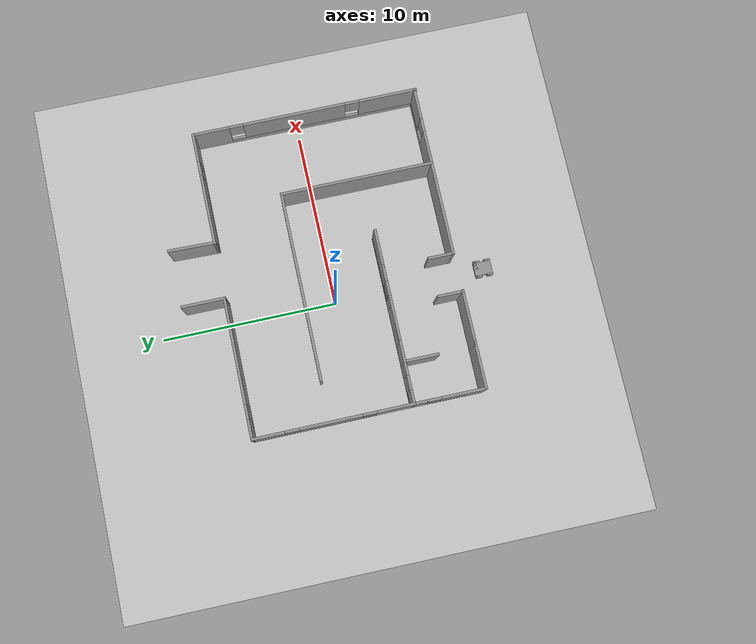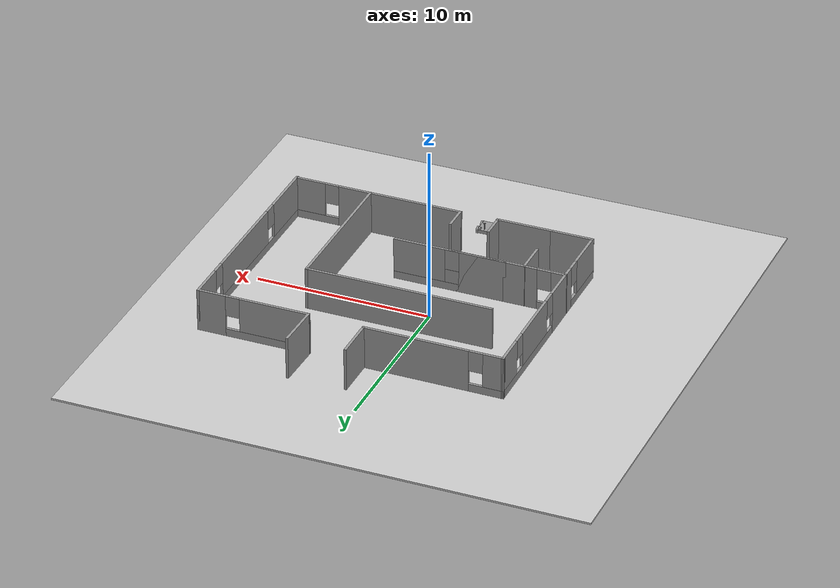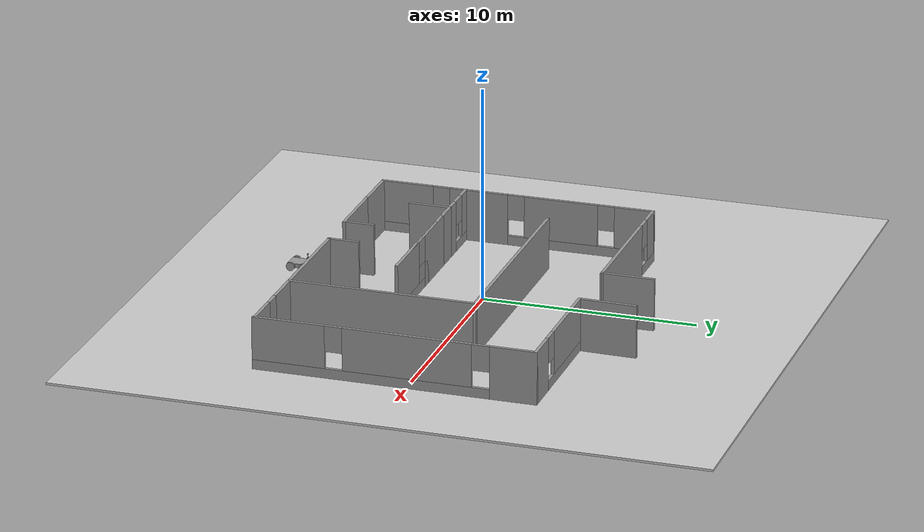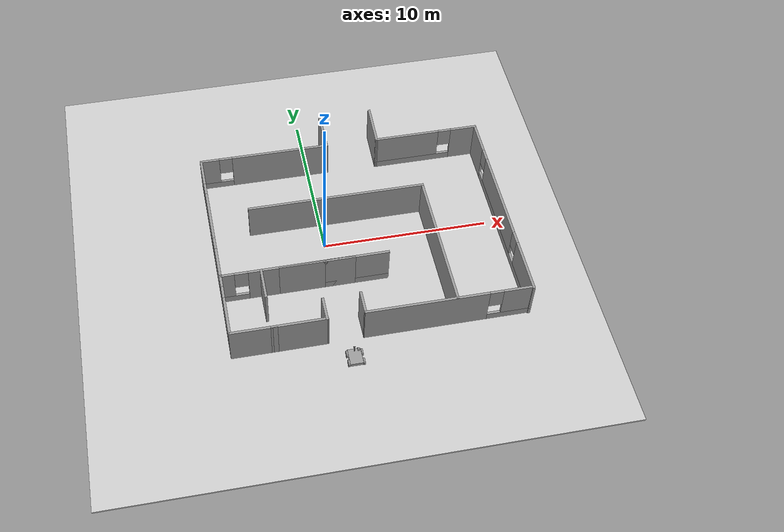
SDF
<?xml version="1.0" ?>

<sdf version="1.6">
  <world name="visualize_lidar_world">
    <physics name="1ms" type="ignored">
      <max_step_size>0.001</max_step_size>
      <real_time_factor>1.0</real_time_factor>
    </physics>
    <plugin
      filename="libignition-gazebo-physics-system.so"
      name="ignition::gazebo::systems::Physics">
    </plugin>
    <plugin
      filename="libignition-gazebo-sensors-system.so"
      name="ignition::gazebo::systems::Sensors">
      <render_engine>ogre2</render_engine>
    </plugin>
    <plugin
      filename="libignition-gazebo-scene-broadcaster-system.so"
      name="ignition::gazebo::systems::SceneBroadcaster">
    </plugin>

    <gui fullscreen="0">

      <!-- 3D scene -->
      <plugin filename="MinimalScene" name="3D View">
        <ignition-gui>
          <title>3D View</title>
          <property type="bool" key="showTitleBar">false</property>
          <property type="string" key="state">docked</property>
        </ignition-gui>

        <engine>ogre2</engine>
        <scene>scene</scene>
        <ambient_light>0.4 0.4 0.4</ambient_light>
        <background_color>0.8 0.8 0.8</background_color>
        <camera_pose>-6 0 6 0 0.5 0</camera_pose>
      </plugin>

      <!-- Plugins that add functionality to the scene -->
      <plugin filename="EntityContextMenuPlugin" name="Entity context menu">
        <ignition-gui>
          <property key="state" type="string">floating</property>
          <property key="width" type="double">5</property>
          <property key="height" type="double">5</property>
          <property key="showTitleBar" type="bool">false</property>
        </ignition-gui>
      </plugin>
      <plugin filename="GzSceneManager" name="Scene Manager">
        <ignition-gui>
          <property key="resizable" type="bool">false</property>
          <property key="width" type="double">5</property>
          <property key="height" type="double">5</property>
          <property key="state" type="string">floating</property>
          <property key="showTitleBar" type="bool">false</property>
        </ignition-gui>
      </plugin>
      <plugin filename="InteractiveViewControl" name="Interactive view control">
        <ignition-gui>
          <property key="resizable" type="bool">false</property>
          <property key="width" type="double">5</property>
          <property key="height" type="double">5</property>
          <property key="state" type="string">floating</property>
          <property key="showTitleBar" type="bool">false</property>
        </ignition-gui>
      </plugin>
      <plugin filename="CameraTracking" name="Camera Tracking">
        <ignition-gui>
          <property key="resizable" type="bool">false</property>
          <property key="width" type="double">5</property>
          <property key="height" type="double">5</property>
          <property key="state" type="string">floating</property>
          <property key="showTitleBar" type="bool">false</property>
        </ignition-gui>
      </plugin>
      <!-- World control -->
      <plugin filename="WorldControl" name="World control">
        <ignition-gui>
          <title>World control</title>
          <property type="bool" key="showTitleBar">false</property>
          <property type="bool" key="resizable">false</property>
          <property type="double" key="height">72</property>
          <property type="double" key="width">121</property>
          <property type="double" key="z">1</property>

          <property type="string" key="state">floating</property>
          <anchors target="3D View">
            <line own="left" target="left"/>
            <line own="bottom" target="bottom"/>
          </anchors>
        </ignition-gui>

        <play_pause>true</play_pause>
        <step>true</step>
        <start_paused>true</start_paused>
        <use_event>true</use_event>

      </plugin>

      <!-- World statistics -->
      <plugin filename="WorldStats" name="World stats">
        <ignition-gui>
          <title>World stats</title>
          <property type="bool" key="showTitleBar">false</property>
          <property type="bool" key="resizable">false</property>
          <property type="double" key="height">110</property>
          <property type="double" key="width">290</property>
          <property type="double" key="z">1</property>

          <property type="string" key="state">floating</property>
          <anchors target="3D View">
            <line own="right" target="right"/>
            <line own="bottom" target="bottom"/>
          </anchors>
        </ignition-gui>

        <sim_time>true</sim_time>
        <real_time>true</real_time>
        <real_time_factor>true</real_time_factor>
        <iterations>true</iterations>
      </plugin>

      <plugin filename="ImageDisplay" name="Image Display">
        <ignition-gui>
          <property key="state" type="string">docked</property>
        </ignition-gui>
      </plugin>

      <!-- Inspector -->
      <plugin filename="ComponentInspector" name="Component inspector">
        <ignition-gui>
          <property type="string" key="state">docked</property>
        </ignition-gui>
      </plugin>

      <!-- Entity tree -->
      <plugin filename="EntityTree" name="Entity tree">
        <ignition-gui>
          <property type="string" key="state">docked</property>
        </ignition-gui>
      </plugin>

      <plugin filename="VisualizeLidar" name="Visualize Lidar">
      </plugin>

    </gui>

    <light type="directional" name="sun">
      <cast_shadows>true</cast_shadows>
      <pose>0 0 10 0 0 0</pose>
      <diffuse>0.8 0.8 0.8 1</diffuse>
      <specular>0.2 0.2 0.2 1</specular>
      <attenuation>
        <range>1000</range>
        <constant>0.9</constant>
        <linear>0.01</linear>
        <quadratic>0.001</quadratic>
      </attenuation>
      <direction>-0.5 0.1 -0.9</direction>
    </light>

    <model name="ground_plane">
      <static>true</static>
      <link name="link">
        <collision name="collision">
          <geometry>
            <box>
              <size>30 30 0.1</size>
            </box>
          </geometry>
        </collision>
        <visual name="visual">
          <geometry>
            <box>
              <size>30 30 0.1</size>
            </box>
          </geometry>
          <material>
            <ambient>0.8 0.8 0.8 1</ambient>
            <diffuse>0.8 0.8 0.8 1</diffuse>
            <specular>0.8 0.8 0.8 1</specular>
          </material>
        </visual>
      </link>
    </model>

    <!-- My own robot -->
    <include>
        <pose>0 -8.5 1 0 0 1.57</pose>
        <uri>../models/land_robot</uri>
    </include>

    <!-- A playground -->

  <model name='Laberint'>
    <pose>2.05042 0.753959 0 0 -0 0</pose>
    <link name='Wall_0'>
      <collision name='Wall_0_Collision'>
        <geometry>
          <box>
            <size>3.27302 0.15 2.5</size>
          </box>
        </geometry>
        <pose>0 0 1.25 0 -0 0</pose>
      </collision>
      <visual name='Wall_0_Visual'>
        <pose>0 0 1.25 0 -0 0</pose>
        <geometry>
          <box>
            <size>3.27302 0.15 2.5</size>
          </box>
        </geometry>
        <material>
          <script>
            <uri>file://media/materials/scripts/gazebo.material</uri>
            <name>Gazebo/Grey</name>
          </script>
          <ambient>1 1 1 1</ambient>
        </material>
        <meta>
          <layer>0</layer>
        </meta>
      </visual>
      <pose>-4.74364 -7.69515 0 0 -0 0.003682</pose>
    </link>
    <link name='Wall_1'>
      <collision name='Wall_1_Collision'>
        <geometry>
          <box>
            <size>1.5 0.15 2.5</size>
          </box>
        </geometry>
        <pose>0 0 1.25 0 -0 0</pose>
      </collision>
      <visual name='Wall_1_Visual'>
        <pose>0 0 1.25 0 -0 0</pose>
        <geometry>
          <box>
            <size>1.5 0.15 2.5</size>
          </box>
        </geometry>
        <material>
          <script>
            <uri>file://media/materials/scripts/gazebo.material</uri>
            <name>Gazebo/Grey</name>
          </script>
          <ambient>1 1 1 1</ambient>
        </material>
        <meta>
          <layer>0</layer>
        </meta>
      </visual>
      <pose>-3.19963 -7.0144 0 0 -0 1.5708</pose>
    </link>
    <link name='Wall_10'>
      <collision name='Wall_10_Collision'>
        <geometry>
          <box>
            <size>4.5 0.15 2.5</size>
          </box>
        </geometry>
        <pose>0 0 1.25 0 -0 0</pose>
      </collision>
      <visual name='Wall_10_Visual'>
        <pose>0 0 1.25 0 -0 0</pose>
        <geometry>
          <box>
            <size>4.5 0.15 2.5</size>
          </box>
        </geometry>
        <material>
          <script>
            <uri>file://media/materials/scripts/gazebo.material</uri>
            <name>Gazebo/Grey</name>
          </script>
          <ambient>1 1 1 1</ambient>
        </material>
        <meta>
          <layer>0</layer>
        </meta>
      </visual>
      <pose>-3.02986 -3.71139 0 0 -0 3.14159</pose>
    </link>
    <link name='Wall_11'>
      <pose>-2.02986 -3.71139 0 0 -0 0</pose>
      <visual name='Wall_11_Visual_0'>
        <pose>-1.89341 0 1.25 0 -0 0</pose>
        <geometry>
          <box>
            <size>2.71319 0.15 2.5</size>
          </box>
        </geometry>
        <material>
          <script>
            <uri>file://media/materials/scripts/gazebo.material</uri>
            <name>Gazebo/Grey</name>
          </script>
          <ambient>1 1 1 1</ambient>
        </material>
        <meta>
          <layer>0</layer>
        </meta>
      </visual>
      <collision name='Wall_11_Collision_0'>
        <geometry>
          <box>
            <size>2.71319 0.15 2.5</size>
          </box>
        </geometry>
        <pose>-1.89341 0 1.25 0 -0 0</pose>
      </collision>
      <visual name='Wall_11_Visual_1'>
        <pose>1.35659 0 0.25 0 -0 0</pose>
        <geometry>
          <box>
            <size>3.78681 0.15 0.5</size>
          </box>
        </geometry>
        <material>
          <script>
            <uri>file://media/materials/scripts/gazebo.material</uri>
            <name>Gazebo/Grey</name>
          </script>
          <ambient>1 1 1 1</ambient>
        </material>
        <meta>
          <layer>0</layer>
        </meta>
      </visual>
      <collision name='Wall_11_Collision_1'>
        <geometry>
          <box>
            <size>3.78681 0.15 0.5</size>
          </box>
        </geometry>
        <pose>1.35659 0 0.25 0 -0 0</pose>
      </collision>
      <visual name='Wall_11_Visual_2'>
        <pose>1.75659 0 1.5 0 -0 0</pose>
        <geometry>
          <box>
            <size>2.98681 0.15 2</size>
          </box>
        </geometry>
        <material>
          <script>
            <uri>file://media/materials/scripts/gazebo.material</uri>
            <name>Gazebo/Grey</name>
          </script>
          <ambient>1 1 1 1</ambient>
        </material>
        <meta>
          <layer>0</layer>
        </meta>
      </visual>
      <collision name='Wall_11_Collision_2'>
        <geometry>
          <box>
            <size>2.98681 0.15 2</size>
          </box>
        </geometry>
        <pose>1.75659 0 1.5 0 -0 0</pose>
      </collision>
      <visual name='Wall_11_Visual_3'>
        <pose>-0.136812 0 1.9 0 -0 0</pose>
        <geometry>
          <box>
            <size>0.8 0.15 1.2</size>
          </box>
        </geometry>
        <material>
          <script>
            <uri>file://media/materials/scripts/gazebo.material</uri>
            <name>Gazebo/Grey</name>
          </script>
          <ambient>1 1 1 1</ambient>
        </material>
        <meta>
          <layer>0</layer>
        </meta>
      </visual>
      <collision name='Wall_11_Collision_3'>
        <geometry>
          <box>
            <size>0.8 0.15 1.2</size>
          </box>
        </geometry>
        <pose>-0.136812 0 1.9 0 -0 0</pose>
      </collision>
    </link>
    <link name='Wall_14'>
      <collision name='Wall_14_Collision'>
        <geometry>
          <box>
            <size>1.25 0.15 2.5</size>
          </box>
        </geometry>
        <pose>0 0 1.25 0 -0 0</pose>
      </collision>
      <visual name='Wall_14_Visual'>
        <pose>0 0 1.25 0 -0 0</pose>
        <geometry>
          <box>
            <size>1.25 0.15 2.5</size>
          </box>
        </geometry>
        <material>
          <script>
            <uri>file://media/materials/scripts/gazebo.material</uri>
            <name>Gazebo/Grey</name>
          </script>
          <ambient>1 1 1 1</ambient>
        </material>
        <meta>
          <layer>0</layer>
        </meta>
      </visual>
      <pose>-5.75486 -3.71139 0 0 -0 3.14159</pose>
    </link>
    <link name='Wall_15'>
      <collision name='Wall_15_Collision'>
        <geometry>
          <box>
            <size>2 0.15 2.5</size>
          </box>
        </geometry>
        <pose>0 0 1.25 0 -0 0</pose>
      </collision>
      <visual name='Wall_15_Visual'>
        <pose>0 0 1.25 0 -0 0</pose>
        <geometry>
          <box>
            <size>2 0.15 2.5</size>
          </box>
        </geometry>
        <material>
          <script>
            <uri>file://media/materials/scripts/gazebo.material</uri>
            <name>Gazebo/Grey</name>
          </script>
          <ambient>1 1 1 1</ambient>
        </material>
        <meta>
          <layer>0</layer>
        </meta>
      </visual>
      <pose>-6.30486 -4.63639 0 0 -0 -1.5708</pose>
    </link>
    <link name='Wall_17'>
      <pose>-7.47986 -3.71139 0 0 -0 3.14159</pose>
      <visual name='Wall_17_Visual_0'>
        <pose>-0.833139 0 1.25 0 -0 0</pose>
        <geometry>
          <box>
            <size>0.833722 0.15 2.5</size>
          </box>
        </geometry>
        <material>
          <script>
            <uri>file://media/materials/scripts/gazebo.material</uri>
            <name>Gazebo/Grey</name>
          </script>
          <ambient>1 1 1 1</ambient>
        </material>
        <meta>
          <layer>0</layer>
        </meta>
      </visual>
      <collision name='Wall_17_Collision_0'>
        <geometry>
          <box>
            <size>0.833722 0.15 2.5</size>
          </box>
        </geometry>
        <pose>-0.833139 0 1.25 0 -0 0</pose>
      </collision>
      <visual name='Wall_17_Visual_1'>
        <pose>0.416861 0 0.25 0 -0 0</pose>
        <geometry>
          <box>
            <size>1.66628 0.15 0.5</size>
          </box>
        </geometry>
        <material>
          <script>
            <uri>file://media/materials/scripts/gazebo.material</uri>
            <name>Gazebo/Grey</name>
          </script>
          <ambient>1 1 1 1</ambient>
        </material>
        <meta>
          <layer>0</layer>
        </meta>
      </visual>
      <collision name='Wall_17_Collision_1'>
        <geometry>
          <box>
            <size>1.66628 0.15 0.5</size>
          </box>
        </geometry>
        <pose>0.416861 0 0.25 0 -0 0</pose>
      </collision>
      <visual name='Wall_17_Visual_2'>
        <pose>0.816861 0 1.5 0 -0 0</pose>
        <geometry>
          <box>
            <size>0.866278 0.15 2</size>
          </box>
        </geometry>
        <material>
          <script>
            <uri>file://media/materials/scripts/gazebo.material</uri>
            <name>Gazebo/Grey</name>
          </script>
          <ambient>1 1 1 1</ambient>
        </material>
        <meta>
          <layer>0</layer>
        </meta>
      </visual>
      <collision name='Wall_17_Collision_2'>
        <geometry>
          <box>
            <size>0.866278 0.15 2</size>
          </box>
        </geometry>
        <pose>0.816861 0 1.5 0 -0 0</pose>
      </collision>
      <visual name='Wall_17_Visual_3'>
        <pose>-0.016278 0 1.9 0 -0 0</pose>
        <geometry>
          <box>
            <size>0.8 0.15 1.2</size>
          </box>
        </geometry>
        <material>
          <script>
            <uri>file://media/materials/scripts/gazebo.material</uri>
            <name>Gazebo/Grey</name>
          </script>
          <ambient>1 1 1 1</ambient>
        </material>
        <meta>
          <layer>0</layer>
        </meta>
      </visual>
      <collision name='Wall_17_Collision_3'>
        <geometry>
          <box>
            <size>0.8 0.15 1.2</size>
          </box>
        </geometry>
        <pose>-0.016278 0 1.9 0 -0 0</pose>
      </collision>
    </link>
    <link name='Wall_18'>
      <pose>-8.65486 -5.7032 0 0 -0 -1.5708</pose>
      <visual name='Wall_18_Visual_0'>
        <pose>-1.6633 0 1.25 0 -0 0</pose>
        <geometry>
          <box>
            <size>0.807023 0.15 2.5</size>
          </box>
        </geometry>
        <material>
          <script>
            <uri>file://media/materials/scripts/gazebo.material</uri>
            <name>Gazebo/Grey</name>
          </script>
          <ambient>1 1 1 1</ambient>
        </material>
        <meta>
          <layer>0</layer>
        </meta>
      </visual>
      <collision name='Wall_18_Collision_0'>
        <geometry>
          <box>
            <size>0.807023 0.15 2.5</size>
          </box>
        </geometry>
        <pose>-1.6633 0 1.25 0 -0 0</pose>
      </collision>
      <visual name='Wall_18_Visual_1'>
        <pose>0.403511 0 0.25 0 -0 0</pose>
        <geometry>
          <box>
            <size>3.3266 0.15 0.5</size>
          </box>
        </geometry>
        <material>
          <script>
            <uri>file://media/materials/scripts/gazebo.material</uri>
            <name>Gazebo/Grey</name>
          </script>
          <ambient>1 1 1 1</ambient>
        </material>
        <meta>
          <layer>0</layer>
        </meta>
      </visual>
      <collision name='Wall_18_Collision_1'>
        <geometry>
          <box>
            <size>3.3266 0.15 0.5</size>
          </box>
        </geometry>
        <pose>0.403511 0 0.25 0 -0 0</pose>
      </collision>
      <visual name='Wall_18_Visual_2'>
        <pose>0.803511 0 1.5 0 -0 0</pose>
        <geometry>
          <box>
            <size>2.5266 0.15 2</size>
          </box>
        </geometry>
        <material>
          <script>
            <uri>file://media/materials/scripts/gazebo.material</uri>
            <name>Gazebo/Grey</name>
          </script>
          <ambient>1 1 1 1</ambient>
        </material>
        <meta>
          <layer>0</layer>
        </meta>
      </visual>
      <collision name='Wall_18_Collision_2'>
        <geometry>
          <box>
            <size>2.5266 0.15 2</size>
          </box>
        </geometry>
        <pose>0.803511 0 1.5 0 -0 0</pose>
      </collision>
      <visual name='Wall_18_Visual_3'>
        <pose>-0.859789 0 1.9 0 -0 0</pose>
        <geometry>
          <box>
            <size>0.8 0.15 1.2</size>
          </box>
        </geometry>
        <material>
          <script>
            <uri>file://media/materials/scripts/gazebo.material</uri>
            <name>Gazebo/Grey</name>
          </script>
          <ambient>1 1 1 1</ambient>
        </material>
        <meta>
          <layer>0</layer>
        </meta>
      </visual>
      <collision name='Wall_18_Collision_3'>
        <geometry>
          <box>
            <size>0.8 0.15 1.2</size>
          </box>
        </geometry>
        <pose>-0.859789 0 1.9 0 -0 0</pose>
      </collision>
    </link>
    <link name='Wall_19'>
      <collision name='Wall_19_Collision'>
        <geometry>
          <box>
            <size>2.75 0.15 2.5</size>
          </box>
        </geometry>
        <pose>0 0 1.25 0 -0 0</pose>
      </collision>
      <visual name='Wall_19_Visual'>
        <pose>0 0 1.25 0 -0 0</pose>
        <geometry>
          <box>
            <size>2.75 0.15 2.5</size>
          </box>
        </geometry>
        <material>
          <script>
            <uri>file://media/materials/scripts/gazebo.material</uri>
            <name>Gazebo/Grey</name>
          </script>
          <ambient>1 1 1 1</ambient>
        </material>
        <meta>
          <layer>0</layer>
        </meta>
      </visual>
      <pose>-7.35486 -7.70073 0 0 -0 0</pose>
    </link>
    <link name='Wall_21'>
      <collision name='Wall_21_Collision'>
        <geometry>
          <box>
            <size>8.75 0.15 2.5</size>
          </box>
        </geometry>
        <pose>0 0 1.25 0 -0 0</pose>
      </collision>
      <visual name='Wall_21_Visual'>
        <pose>0 0 1.25 0 -0 0</pose>
        <geometry>
          <box>
            <size>8.75 0.15 2.5</size>
          </box>
        </geometry>
        <material>
          <script>
            <uri>file://media/materials/scripts/gazebo.material</uri>
            <name>Gazebo/Grey</name>
          </script>
          <ambient>1 1 1 1</ambient>
        </material>
        <meta>
          <layer>0</layer>
        </meta>
      </visual>
      <pose>4.28676 -3.34222 0 0 -0 1.5708</pose>
    </link>
    <link name='Wall_23'>
      <collision name='Wall_23_Collision'>
        <geometry>
          <box>
            <size>10.75 0.15 2.5</size>
          </box>
        </geometry>
        <pose>0 0 1.25 0 -0 0</pose>
      </collision>
      <visual name='Wall_23_Visual'>
        <pose>0 0 1.25 0 -0 0</pose>
        <geometry>
          <box>
            <size>10.75 0.15 2.5</size>
          </box>
        </geometry>
        <material>
          <script>
            <uri>file://media/materials/scripts/gazebo.material</uri>
            <name>Gazebo/Grey</name>
          </script>
          <ambient>1 1 1 1</ambient>
        </material>
        <meta>
          <layer>0</layer>
        </meta>
      </visual>
      <pose>-1.01324 0.957785 0 0 -0 3.14159</pose>
    </link>
    <link name='Wall_25'>
      <pose>-8.67483 0.766379 0 0 -0 1.57526</pose>
      <visual name='Wall_25_Visual_0'>
        <pose>-3.49076 0 1.25 0 -0 0</pose>
        <geometry>
          <box>
            <size>2.12409 0.15 2.5</size>
          </box>
        </geometry>
        <material>
          <script>
            <uri>file://media/materials/scripts/gazebo.material</uri>
            <name>Gazebo/Grey</name>
          </script>
          <ambient>1 1 1 1</ambient>
        </material>
        <meta>
          <layer>0</layer>
        </meta>
      </visual>
      <collision name='Wall_25_Collision_0'>
        <geometry>
          <box>
            <size>2.12409 0.15 2.5</size>
          </box>
        </geometry>
        <pose>-3.49076 0 1.25 0 -0 0</pose>
      </collision>
      <visual name='Wall_25_Visual_1'>
        <pose>1.06204 0 0.25 0 -0 0</pose>
        <geometry>
          <box>
            <size>6.98152 0.15 0.5</size>
          </box>
        </geometry>
        <material>
          <script>
            <uri>file://media/materials/scripts/gazebo.material</uri>
            <name>Gazebo/Grey</name>
          </script>
          <ambient>1 1 1 1</ambient>
        </material>
        <meta>
          <layer>0</layer>
        </meta>
      </visual>
      <collision name='Wall_25_Collision_1'>
        <geometry>
          <box>
            <size>6.98152 0.15 0.5</size>
          </box>
        </geometry>
        <pose>1.06204 0 0.25 0 -0 0</pose>
      </collision>
      <visual name='Wall_25_Visual_2'>
        <pose>0.121712 0 1.5 0 -0 0</pose>
        <geometry>
          <box>
            <size>3.50086 0.15 2</size>
          </box>
        </geometry>
        <material>
          <script>
            <uri>file://media/materials/scripts/gazebo.material</uri>
            <name>Gazebo/Grey</name>
          </script>
          <ambient>1 1 1 1</ambient>
        </material>
        <meta>
          <layer>0</layer>
        </meta>
      </visual>
      <collision name='Wall_25_Collision_2'>
        <geometry>
          <box>
            <size>3.50086 0.15 2</size>
          </box>
        </geometry>
        <pose>0.121712 0 1.5 0 -0 0</pose>
      </collision>
      <visual name='Wall_25_Visual_3'>
        <pose>3.61247 0 1.5 0 -0 0</pose>
        <geometry>
          <box>
            <size>1.88066 0.15 2</size>
          </box>
        </geometry>
        <material>
          <script>
            <uri>file://media/materials/scripts/gazebo.material</uri>
            <name>Gazebo/Grey</name>
          </script>
          <ambient>1 1 1 1</ambient>
        </material>
        <meta>
          <layer>0</layer>
        </meta>
      </visual>
      <collision name='Wall_25_Collision_3'>
        <geometry>
          <box>
            <size>1.88066 0.15 2</size>
          </box>
        </geometry>
        <pose>3.61247 0 1.5 0 -0 0</pose>
      </collision>
      <visual name='Wall_25_Visual_4'>
        <pose>-2.02872 0 1.9 0 -0 0</pose>
        <geometry>
          <box>
            <size>0.8 0.15 1.2</size>
          </box>
        </geometry>
        <material>
          <script>
            <uri>file://media/materials/scripts/gazebo.material</uri>
            <name>Gazebo/Grey</name>
          </script>
          <ambient>1 1 1 1</ambient>
        </material>
        <meta>
          <layer>0</layer>
        </meta>
      </visual>
      <collision name='Wall_25_Collision_4'>
        <geometry>
          <box>
            <size>0.8 0.15 1.2</size>
          </box>
        </geometry>
        <pose>-2.02872 0 1.9 0 -0 0</pose>
      </collision>
      <visual name='Wall_25_Visual_5'>
        <pose>2.27214 0 1.9 0 -0 0</pose>
        <geometry>
          <box>
            <size>0.8 0.15 1.2</size>
          </box>
        </geometry>
        <material>
          <script>
            <uri>file://media/materials/scripts/gazebo.material</uri>
            <name>Gazebo/Grey</name>
          </script>
          <ambient>1 1 1 1</ambient>
        </material>
        <meta>
          <layer>0</layer>
        </meta>
      </visual>
      <collision name='Wall_25_Collision_5'>
        <geometry>
          <box>
            <size>0.8 0.15 1.2</size>
          </box>
        </geometry>
        <pose>2.27214 0 1.9 0 -0 0</pose>
      </collision>
    </link>
    <link name='Wall_28'>
      <pose>8.69514 -1.28639 0 0 -0 -1.5708</pose>
      <visual name='Wall_28_Visual_0'>
        <pose>-5.42418 0 1.25 0 -0 0</pose>
        <geometry>
          <box>
            <size>2.15163 0.15 2.5</size>
          </box>
        </geometry>
        <material>
          <script>
            <uri>file://media/materials/scripts/gazebo.material</uri>
            <name>Gazebo/Grey</name>
          </script>
          <ambient>1 1 1 1</ambient>
        </material>
        <meta>
          <layer>0</layer>
        </meta>
      </visual>
      <collision name='Wall_28_Collision_0'>
        <geometry>
          <box>
            <size>2.15163 0.15 2.5</size>
          </box>
        </geometry>
        <pose>-5.42418 0 1.25 0 -0 0</pose>
      </collision>
      <visual name='Wall_28_Visual_1'>
        <pose>1.07582 0 0.25 0 -0 0</pose>
        <geometry>
          <box>
            <size>10.8484 0.15 0.5</size>
          </box>
        </geometry>
        <material>
          <script>
            <uri>file://media/materials/scripts/gazebo.material</uri>
            <name>Gazebo/Grey</name>
          </script>
          <ambient>1 1 1 1</ambient>
        </material>
        <meta>
          <layer>0</layer>
        </meta>
      </visual>
      <collision name='Wall_28_Collision_1'>
        <geometry>
          <box>
            <size>10.8484 0.15 0.5</size>
          </box>
        </geometry>
        <pose>1.07582 0 0.25 0 -0 0</pose>
      </collision>
      <visual name='Wall_28_Visual_2'>
        <pose>-0.59885 0 1.5 0 -0 0</pose>
        <geometry>
          <box>
            <size>5.89903 0.15 2</size>
          </box>
        </geometry>
        <material>
          <script>
            <uri>file://media/materials/scripts/gazebo.material</uri>
            <name>Gazebo/Grey</name>
          </script>
          <ambient>1 1 1 1</ambient>
        </material>
        <meta>
          <layer>0</layer>
        </meta>
      </visual>
      <collision name='Wall_28_Collision_2'>
        <geometry>
          <box>
            <size>5.89903 0.15 2</size>
          </box>
        </geometry>
        <pose>-0.59885 0 1.5 0 -0 0</pose>
      </collision>
      <visual name='Wall_28_Visual_3'>
        <pose>4.82533 0 1.5 0 -0 0</pose>
        <geometry>
          <box>
            <size>3.34933 0.15 2</size>
          </box>
        </geometry>
        <material>
          <script>
            <uri>file://media/materials/scripts/gazebo.material</uri>
            <name>Gazebo/Grey</name>
          </script>
          <ambient>1 1 1 1</ambient>
        </material>
        <meta>
          <layer>0</layer>
        </meta>
      </visual>
      <collision name='Wall_28_Collision_3'>
        <geometry>
          <box>
            <size>3.34933 0.15 2</size>
          </box>
        </geometry>
        <pose>4.82533 0 1.5 0 -0 0</pose>
      </collision>
      <visual name='Wall_28_Visual_4'>
        <pose>-3.94837 0 1.9 0 -0 0</pose>
        <geometry>
          <box>
            <size>0.8 0.15 1.2</size>
          </box>
        </geometry>
        <material>
          <script>
            <uri>file://media/materials/scripts/gazebo.material</uri>
            <name>Gazebo/Grey</name>
          </script>
          <ambient>1 1 1 1</ambient>
        </material>
        <meta>
          <layer>0</layer>
        </meta>
      </visual>
      <collision name='Wall_28_Collision_4'>
        <geometry>
          <box>
            <size>0.8 0.15 1.2</size>
          </box>
        </geometry>
        <pose>-3.94837 0 1.9 0 -0 0</pose>
      </collision>
      <visual name='Wall_28_Visual_5'>
        <pose>2.75067 0 1.9 0 -0 0</pose>
        <geometry>
          <box>
            <size>0.8 0.15 1.2</size>
          </box>
        </geometry>
        <material>
          <script>
            <uri>file://media/materials/scripts/gazebo.material</uri>
            <name>Gazebo/Grey</name>
          </script>
          <ambient>1 1 1 1</ambient>
        </material>
        <meta>
          <layer>0</layer>
        </meta>
      </visual>
      <collision name='Wall_28_Collision_5'>
        <geometry>
          <box>
            <size>0.8 0.15 1.2</size>
          </box>
        </geometry>
        <pose>2.75067 0 1.9 0 -0 0</pose>
      </collision>
    </link>
    <link name='Wall_3'>
      <collision name='Wall_3_Collision'>
        <geometry>
          <box>
            <size>1.5 0.15 2.5</size>
          </box>
        </geometry>
        <pose>0 0 1.25 0 -0 0</pose>
      </collision>
      <visual name='Wall_3_Visual'>
        <pose>0 0 1.25 0 -0 0</pose>
        <geometry>
          <box>
            <size>1.5 0.15 2.5</size>
          </box>
        </geometry>
        <material>
          <script>
            <uri>file://media/materials/scripts/gazebo.material</uri>
            <name>Gazebo/Grey</name>
          </script>
          <ambient>1 1 1 1</ambient>
        </material>
        <meta>
          <layer>0</layer>
        </meta>
      </visual>
      <pose>-1.00921 -6.97938 0 0 -0 -1.5708</pose>
    </link>
    <link name='Wall_31'>
      <pose>5.52014 5.13861 0 0 -0 3.14159</pose>
      <visual name='Wall_31_Visual_0'>
        <pose>-2.41938 0 1.25 0 -0 0</pose>
        <geometry>
          <box>
            <size>1.66123 0.15 2.5</size>
          </box>
        </geometry>
        <material>
          <script>
            <uri>file://media/materials/scripts/gazebo.material</uri>
            <name>Gazebo/Grey</name>
          </script>
          <ambient>1 1 1 1</ambient>
        </material>
        <meta>
          <layer>0</layer>
        </meta>
      </visual>
      <collision name='Wall_31_Collision_0'>
        <geometry>
          <box>
            <size>1.66123 0.15 2.5</size>
          </box>
        </geometry>
        <pose>-2.41938 0 1.25 0 -0 0</pose>
      </collision>
      <visual name='Wall_31_Visual_1'>
        <pose>0.830617 0 0.25 0 -0 0</pose>
        <geometry>
          <box>
            <size>4.83877 0.15 0.5</size>
          </box>
        </geometry>
        <material>
          <script>
            <uri>file://media/materials/scripts/gazebo.material</uri>
            <name>Gazebo/Grey</name>
          </script>
          <ambient>1 1 1 1</ambient>
        </material>
        <meta>
          <layer>0</layer>
        </meta>
      </visual>
      <collision name='Wall_31_Collision_1'>
        <geometry>
          <box>
            <size>4.83877 0.15 0.5</size>
          </box>
        </geometry>
        <pose>0.830617 0 0.25 0 -0 0</pose>
      </collision>
      <visual name='Wall_31_Visual_2'>
        <pose>1.23062 0 1.5 0 -0 0</pose>
        <geometry>
          <box>
            <size>4.03877 0.15 2</size>
          </box>
        </geometry>
        <material>
          <script>
            <uri>file://media/materials/scripts/gazebo.material</uri>
            <name>Gazebo/Grey</name>
          </script>
          <ambient>1 1 1 1</ambient>
        </material>
        <meta>
          <layer>0</layer>
        </meta>
      </visual>
      <collision name='Wall_31_Collision_2'>
        <geometry>
          <box>
            <size>4.03877 0.15 2</size>
          </box>
        </geometry>
        <pose>1.23062 0 1.5 0 -0 0</pose>
      </collision>
      <visual name='Wall_31_Visual_3'>
        <pose>-1.18877 0 1.9 0 -0 0</pose>
        <geometry>
          <box>
            <size>0.8 0.15 1.2</size>
          </box>
        </geometry>
        <material>
          <script>
            <uri>file://media/materials/scripts/gazebo.material</uri>
            <name>Gazebo/Grey</name>
          </script>
          <ambient>1 1 1 1</ambient>
        </material>
        <meta>
          <layer>0</layer>
        </meta>
      </visual>
      <collision name='Wall_31_Collision_3'>
        <geometry>
          <box>
            <size>0.8 0.15 1.2</size>
          </box>
        </geometry>
        <pose>-1.18877 0 1.9 0 -0 0</pose>
      </collision>
    </link>
    <link name='Wall_33'>
      <pose>-4.76102 5.22985 0 0 -0 3.13796</pose>
      <visual name='Wall_33_Visual_0'>
        <pose>-0.994905 0 1.25 0 -0 0</pose>
        <geometry>
          <box>
            <size>6.0278 0.15 2.5</size>
          </box>
        </geometry>
        <material>
          <script>
            <uri>file://media/materials/scripts/gazebo.material</uri>
            <name>Gazebo/Grey</name>
          </script>
          <ambient>1 1 1 1</ambient>
        </material>
        <meta>
          <layer>0</layer>
        </meta>
      </visual>
      <collision name='Wall_33_Collision_0'>
        <geometry>
          <box>
            <size>6.0278 0.15 2.5</size>
          </box>
        </geometry>
        <pose>-0.994905 0 1.25 0 -0 0</pose>
      </collision>
      <visual name='Wall_33_Visual_1'>
        <pose>3.0139 0 0.25 0 -0 0</pose>
        <geometry>
          <box>
            <size>1.98981 0.15 0.5</size>
          </box>
        </geometry>
        <material>
          <script>
            <uri>file://media/materials/scripts/gazebo.material</uri>
            <name>Gazebo/Grey</name>
          </script>
          <ambient>1 1 1 1</ambient>
        </material>
        <meta>
          <layer>0</layer>
        </meta>
      </visual>
      <collision name='Wall_33_Collision_1'>
        <geometry>
          <box>
            <size>1.98981 0.15 0.5</size>
          </box>
        </geometry>
        <pose>3.0139 0 0.25 0 -0 0</pose>
      </collision>
      <visual name='Wall_33_Visual_2'>
        <pose>3.4139 0 1.5 0 -0 0</pose>
        <geometry>
          <box>
            <size>1.18981 0.15 2</size>
          </box>
        </geometry>
        <material>
          <script>
            <uri>file://media/materials/scripts/gazebo.material</uri>
            <name>Gazebo/Grey</name>
          </script>
          <ambient>1 1 1 1</ambient>
        </material>
        <meta>
          <layer>0</layer>
        </meta>
      </visual>
      <collision name='Wall_33_Collision_2'>
        <geometry>
          <box>
            <size>1.18981 0.15 2</size>
          </box>
        </geometry>
        <pose>3.4139 0 1.5 0 -0 0</pose>
      </collision>
      <visual name='Wall_33_Visual_3'>
        <pose>2.419 0 1.9 0 -0 0</pose>
        <geometry>
          <box>
            <size>0.8 0.15 1.2</size>
          </box>
        </geometry>
        <material>
          <script>
            <uri>file://media/materials/scripts/gazebo.material</uri>
            <name>Gazebo/Grey</name>
          </script>
          <ambient>1 1 1 1</ambient>
        </material>
        <meta>
          <layer>0</layer>
        </meta>
      </visual>
      <collision name='Wall_33_Collision_3'>
        <geometry>
          <box>
            <size>0.8 0.15 1.2</size>
          </box>
        </geometry>
        <pose>2.419 0 1.9 0 -0 0</pose>
      </collision>
    </link>
    <link name='Wall_35'>
      <collision name='Wall_35_Collision'>
        <geometry>
          <box>
            <size>2.5 0.15 2.5</size>
          </box>
        </geometry>
        <pose>0 0 1.25 0 -0 0</pose>
      </collision>
      <visual name='Wall_35_Visual'>
        <pose>0 0 1.25 0 -0 0</pose>
        <geometry>
          <box>
            <size>2.5 0.15 2.5</size>
          </box>
        </geometry>
        <material>
          <script>
            <uri>file://media/materials/scripts/gazebo.material</uri>
            <name>Gazebo/Grey</name>
          </script>
          <ambient>1 1 1 1</ambient>
        </material>
        <meta>
          <layer>0</layer>
        </meta>
      </visual>
      <pose>-0.827241 6.39055 0 0 -0 1.5708</pose>
    </link>
    <link name='Wall_37'>
      <collision name='Wall_37_Collision'>
        <geometry>
          <box>
            <size>2.72173 0.15 2.5</size>
          </box>
        </geometry>
        <pose>0 0 1.25 0 -0 0</pose>
      </collision>
      <visual name='Wall_37_Visual'>
        <pose>0 0 1.25 0 -0 0</pose>
        <geometry>
          <box>
            <size>2.72173 0.15 2.5</size>
          </box>
        </geometry>
        <material>
          <script>
            <uri>file://media/materials/scripts/gazebo.material</uri>
            <name>Gazebo/Grey</name>
          </script>
          <ambient>1 1 1 1</ambient>
        </material>
        <meta>
          <layer>0</layer>
        </meta>
      </visual>
      <pose>2.37797 6.42406 0 0 -0 1.54526</pose>
    </link>
    <link name='Wall_4'>
      <collision name='Wall_4_Collision'>
        <geometry>
          <box>
            <size>0.15 0.15 2.5</size>
          </box>
        </geometry>
        <pose>0 0 1.25 0 -0 0</pose>
      </collision>
      <visual name='Wall_4_Visual'>
        <pose>0 0 1.25 0 -0 0</pose>
        <geometry>
          <box>
            <size>0.15 0.15 2.5</size>
          </box>
        </geometry>
        <material>
          <script>
            <uri>file://media/materials/scripts/gazebo.material</uri>
            <name>Gazebo/Grey</name>
          </script>
          <ambient>1 1 1 1</ambient>
        </material>
        <meta>
          <layer>0</layer>
        </meta>
      </visual>
      <pose>-1.01493 -7.65438 0 0 -0 0</pose>
    </link>
    <link name='Wall_7'>
      <pose>3.81338 -7.65714 0 0 -0 0</pose>
      <visual name='Wall_7_Visual_0'>
        <pose>-1.26404 0 1.25 0 -0 0</pose>
        <geometry>
          <box>
            <size>7.22192 0.15 2.5</size>
          </box>
        </geometry>
        <material>
          <script>
            <uri>file://media/materials/scripts/gazebo.material</uri>
            <name>Gazebo/Grey</name>
          </script>
          <ambient>1 1 1 1</ambient>
        </material>
        <meta>
          <layer>0</layer>
        </meta>
      </visual>
      <collision name='Wall_7_Collision_0'>
        <geometry>
          <box>
            <size>7.22192 0.15 2.5</size>
          </box>
        </geometry>
        <pose>-1.26404 0 1.25 0 -0 0</pose>
      </collision>
      <visual name='Wall_7_Visual_1'>
        <pose>3.61096 0 0.25 0 -0 0</pose>
        <geometry>
          <box>
            <size>2.52808 0.15 0.5</size>
          </box>
        </geometry>
        <material>
          <script>
            <uri>file://media/materials/scripts/gazebo.material</uri>
            <name>Gazebo/Grey</name>
          </script>
          <ambient>1 1 1 1</ambient>
        </material>
        <meta>
          <layer>0</layer>
        </meta>
      </visual>
      <collision name='Wall_7_Collision_1'>
        <geometry>
          <box>
            <size>2.52808 0.15 0.5</size>
          </box>
        </geometry>
        <pose>3.61096 0 0.25 0 -0 0</pose>
      </collision>
      <visual name='Wall_7_Visual_2'>
        <pose>4.01096 0 1.5 0 -0 0</pose>
        <geometry>
          <box>
            <size>1.72808 0.15 2</size>
          </box>
        </geometry>
        <material>
          <script>
            <uri>file://media/materials/scripts/gazebo.material</uri>
            <name>Gazebo/Grey</name>
          </script>
          <ambient>1 1 1 1</ambient>
        </material>
        <meta>
          <layer>0</layer>
        </meta>
      </visual>
      <collision name='Wall_7_Collision_2'>
        <geometry>
          <box>
            <size>1.72808 0.15 2</size>
          </box>
        </geometry>
        <pose>4.01096 0 1.5 0 -0 0</pose>
      </collision>
      <visual name='Wall_7_Visual_3'>
        <pose>2.74692 0 1.9 0 -0 0</pose>
        <geometry>
          <box>
            <size>0.8 0.15 1.2</size>
          </box>
        </geometry>
        <material>
          <script>
            <uri>file://media/materials/scripts/gazebo.material</uri>
            <name>Gazebo/Grey</name>
          </script>
          <ambient>1 1 1 1</ambient>
        </material>
        <meta>
          <layer>0</layer>
        </meta>
      </visual>
      <collision name='Wall_7_Collision_3'>
        <geometry>
          <box>
            <size>0.8 0.15 1.2</size>
          </box>
        </geometry>
        <pose>2.74692 0 1.9 0 -0 0</pose>
      </collision>
    </link>
    <static>1</static>
  </model>

  </world>
</sdf>

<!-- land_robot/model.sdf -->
<sdf version='1.7'>
    <model name='land_robot'>

        <pose>0 0 1 0 0.0 3.14</pose>

        <link name="base_footprint">
          <pose>-0.110726 -0.145588 -0.265574 0 -0 0</pose>
        </link>

        <link name='base_link'>

          <inertial>
            <mass>5</mass>
            <inertia>
              <ixx>0.166667</ixx>
              <ixy>0</ixy>
              <ixz>0</ixz>
              <iyy>0.166667</iyy>
              <iyz>0</iyz>
              <izz>0.166667</izz>
            </inertia>
            <pose>0 0 0 0 -0 0</pose>
          </inertial>

          <pose>-0.110726 -0.145588 -0.265574 0 -0 0</pose>
          <gravity>1</gravity>
          <self_collide>0</self_collide>
          <kinematic>0</kinematic>
          <enable_wind>0</enable_wind>

          <visual name='visual'>
            <pose>0 0 0 0 -0 0</pose>
            <geometry>
              <box>
                <size>1 0.75 0.2</size>
              </box>
            </geometry>
            <material>
              <lighting>1</lighting>
              <script>
                <uri>file://media/materials/scripts/gazebo.material</uri>
                <name>Gazebo/Grey</name>
              </script>
              <shader type='pixel'>
                <normal_map>__default__</normal_map>
              </shader>
              <ambient>0.1 0.1 0.1 1</ambient>
              <diffuse>0.1 0.1 0.1 1</diffuse>
              <specular>0.1 0.1 0.1 1</specular>
              <emissive>0 0 0 1</emissive>
            </material>
            <transparency>0</transparency>
            <cast_shadows>1</cast_shadows>
          </visual>

          <collision name='collision'>
            <laser_retro>0</laser_retro>
            <max_contacts>10</max_contacts>
            <pose>0 0 0 0 -0 0</pose>
            <geometry>
              <box>
                <size>1 0.75 0.2</size>
              </box>
            </geometry>
            <surface>
              <friction>
                <ode>
                  <mu>1</mu>
                  <mu2>1</mu2>
                  <fdir1>0 0 0</fdir1>
                  <slip1>0</slip1>
                  <slip2>0</slip2>
                </ode>
                <torsional>
                  <coefficient>1</coefficient>
                  <patch_radius>0</patch_radius>
                  <surface_radius>0</surface_radius>
                  <use_patch_radius>1</use_patch_radius>
                  <ode>
                    <slip>0</slip>
                  </ode>
                </torsional>
              </friction>
              <bounce>
                <restitution_coefficient>0</restitution_coefficient>
                <threshold>1e+06</threshold>
              </bounce>
              <contact>
                <collide_without_contact>0</collide_without_contact>
                <collide_without_contact_bitmask>1</collide_without_contact_bitmask>
                <collide_bitmask>1</collide_bitmask>
                <ode>
                  <soft_cfm>0</soft_cfm>
                  <soft_erp>0.2</soft_erp>
                  <kp>1e+13</kp>
                  <kd>1</kd>
                  <max_vel>0.01</max_vel>
                  <min_depth>0</min_depth>
                </ode>
                <bullet>
                  <split_impulse>1</split_impulse>
                  <split_impulse_penetration_threshold>-0.01</split_impulse_penetration_threshold>
                  <soft_cfm>0</soft_cfm>
                  <soft_erp>0.2</soft_erp>
                  <kp>1e+13</kp>
                  <kd>1</kd>
                </bullet>
              </contact>
            </surface>
          </collision>

        </link>

        <link name='rueda_der_tras'>
          <inertial>
            <mass>5</mass>
            <inertia>
              <ixx>0.145833</ixx>
              <ixy>0</ixy>
              <ixz>0</ixz>
              <iyy>0.145833</iyy>
              <iyz>0</iyz>
              <izz>0.125</izz>
            </inertia>
            <pose>0 0 0 0 -0 0</pose>
          </inertial>
          <pose>-0.437626 -0.571744 -0.298299 1.5708 -0 0</pose>
          <gravity>1</gravity>
          <self_collide>0</self_collide>
          <kinematic>0</kinematic>
          <enable_wind>0</enable_wind>
          <visual name='visual'>
            <pose>0 0 0 0 -0 0</pose>
            <geometry>
              <cylinder>
                <radius>0.2</radius>
                <length>0.1</length>
              </cylinder>
            </geometry>
            <material>
              <lighting>1</lighting>
              <script>
                <uri>file://media/materials/scripts/gazebo.material</uri>
                <name>Gazebo/Grey</name>
              </script>
              <shader type='pixel'>
                <normal_map>__default__</normal_map>
              </shader>
              <ambient>0.3 0.3 0.3 1</ambient>
              <diffuse>0.7 0.7 0.7 1</diffuse>
              <specular>0.01 0.01 0.01 1</specular>
              <emissive>0 0 0 1</emissive>
            </material>
            <transparency>0</transparency>
            <cast_shadows>1</cast_shadows>
          </visual>
          <collision name='collision'>
            <laser_retro>0</laser_retro>
            <max_contacts>10</max_contacts>
            <pose>0 0 0 0 -0 0</pose>
            <geometry>
              <cylinder>
                <radius>0.2</radius>
                <length>0.1</length>
              </cylinder>
            </geometry>
            <surface>
              <friction>
                <ode>
                  <mu>0.1</mu>
                  <mu2>0.1</mu2>
                  <fdir1>0 0 0</fdir1>
                  <slip1>0</slip1>
                  <slip2>0</slip2>
                </ode>
                <torsional>
                  <coefficient>1</coefficient>
                  <patch_radius>0</patch_radius>
                  <surface_radius>0</surface_radius>
                  <use_patch_radius>1</use_patch_radius>
                  <ode>
                    <slip>0</slip>
                  </ode>
                </torsional>
              </friction>
              <bounce>
                <restitution_coefficient>0</restitution_coefficient>
                <threshold>1e+06</threshold>
              </bounce>
              <contact>
                <collide_without_contact>0</collide_without_contact>
                <collide_without_contact_bitmask>1</collide_without_contact_bitmask>
                <collide_bitmask>1</collide_bitmask>
                <ode>
                  <soft_cfm>0</soft_cfm>
                  <soft_erp>0.2</soft_erp>
                  <kp>1e+13</kp>
                  <kd>1</kd>
                  <max_vel>0.01</max_vel>
                  <min_depth>0</min_depth>
                </ode>
                <bullet>
                  <split_impulse>1</split_impulse>
                  <split_impulse_penetration_threshold>-0.01</split_impulse_penetration_threshold>
                  <soft_cfm>0</soft_cfm>
                  <soft_erp>0.2</soft_erp>
                  <kp>1e+13</kp>
                  <kd>1</kd>
                </bullet>
              </contact>
            </surface>
          </collision>
        </link>

        <link name='rueda_der_del'>
          <inertial>
            <mass>5</mass>
            <inertia>
              <ixx>0.145833</ixx>
              <ixy>0</ixy>
              <ixz>0</ixz>
              <iyy>0.145833</iyy>
              <iyz>0</iyz>
              <izz>0.125</izz>
            </inertia>
            <pose>0 0 0 0 -0 0</pose>
          </inertial>
          <pose>0.171311 -0.571744 -0.298299 1.5708 -0 0</pose>
          <gravity>1</gravity>
          <self_collide>0</self_collide>
          <kinematic>0</kinematic>
          <enable_wind>0</enable_wind>
          <visual name='visual'>
            <pose>0 0 0 0 -0 0</pose>
            <geometry>
              <cylinder>
                <radius>0.2</radius>
                <length>0.1</length>
              </cylinder>
            </geometry>
            <material>
              <lighting>1</lighting>
              <script>
                <uri>file://media/materials/scripts/gazebo.material</uri>
                <name>Gazebo/Grey</name>
              </script>
              <shader type='pixel'>
                <normal_map>__default__</normal_map>
              </shader>
              <ambient>0.3 0.3 0.3 1</ambient>
              <diffuse>0.7 0.7 0.7 1</diffuse>
              <specular>0.01 0.01 0.01 1</specular>
              <emissive>0 0 0 1</emissive>
            </material>
            <transparency>0</transparency>
            <cast_shadows>1</cast_shadows>
          </visual>
          <collision name='collision'>
            <laser_retro>0</laser_retro>
            <max_contacts>10</max_contacts>
            <pose>0 0 0 0 -0 0</pose>
            <geometry>
              <cylinder>
                <radius>0.2</radius>
                <length>0.1</length>
              </cylinder>
            </geometry>
            <surface>
              <friction>
                <ode>
                  <mu>1</mu>
                  <mu2>1</mu2>
                  <fdir1>0 0 0</fdir1>
                  <slip1>0</slip1>
                  <slip2>0</slip2>
                </ode>
                <torsional>
                  <coefficient>1</coefficient>
                  <patch_radius>0</patch_radius>
                  <surface_radius>0</surface_radius>
                  <use_patch_radius>1</use_patch_radius>
                  <ode>
                    <slip>0</slip>
                  </ode>
                </torsional>
              </friction>
              <bounce>
                <restitution_coefficient>0</restitution_coefficient>
                <threshold>1e+06</threshold>
              </bounce>
              <contact>
                <collide_without_contact>0</collide_without_contact>
                <collide_without_contact_bitmask>1</collide_without_contact_bitmask>
                <collide_bitmask>1</collide_bitmask>
                <ode>
                  <soft_cfm>0</soft_cfm>
                  <soft_erp>0.2</soft_erp>
                  <kp>1e+13</kp>
                  <kd>1</kd>
                  <max_vel>0.01</max_vel>
                  <min_depth>0</min_depth>
                </ode>
                <bullet>
                  <split_impulse>1</split_impulse>
                  <split_impulse_penetration_threshold>-0.01</split_impulse_penetration_threshold>
                  <soft_cfm>0</soft_cfm>
                  <soft_erp>0.2</soft_erp>
                  <kp>1e+13</kp>
                  <kd>1</kd>
                </bullet>
              </contact>
            </surface>
          </collision>
        </link>

        <link name='rueda_izq_tras'>
          <inertial>
            <mass>5</mass>
            <inertia>
              <ixx>0.145833</ixx>
              <ixy>0</ixy>
              <ixz>0</ixz>
              <iyy>0.145833</iyy>
              <iyz>0</iyz>
              <izz>0.125</izz>
            </inertia>
            <pose>0 0 0 0 -0 0</pose>
          </inertial>
          <pose>-0.437626 0.280995 -0.298299 1.5708 -0 0</pose>
          <gravity>1</gravity>
          <self_collide>0</self_collide>
          <kinematic>0</kinematic>
          <enable_wind>0</enable_wind>
          <visual name='visual'>
            <pose>0 0 0 0 -0 0</pose>
            <geometry>
              <cylinder>
                <radius>0.2</radius>
                <length>0.1</length>
              </cylinder>
            </geometry>
            <material>
              <lighting>1</lighting>
              <script>
                <uri>file://media/materials/scripts/gazebo.material</uri>
                <name>Gazebo/Grey</name>
              </script>
              <shader type='pixel'>
                <normal_map>__default__</normal_map>
              </shader>
              <ambient>0.3 0.3 0.3 1</ambient>
              <diffuse>0.7 0.7 0.7 1</diffuse>
              <specular>0.01 0.01 0.01 1</specular>
              <emissive>0 0 0 1</emissive>
            </material>
            <transparency>0</transparency>
            <cast_shadows>1</cast_shadows>
          </visual>
          <collision name='collision'>
            <laser_retro>0</laser_retro>
            <max_contacts>10</max_contacts>
            <pose>0 0 0 0 -0 0</pose>
            <geometry>
              <cylinder>
                <radius>0.2</radius>
                <length>0.1</length>
              </cylinder>
            </geometry>
            <surface>
              <friction>
                <ode>
                  <mu>0.1</mu>
                  <mu2>0.1</mu2>
                  <fdir1>0 0 0</fdir1>
                  <slip1>0</slip1>
                  <slip2>0</slip2>
                </ode>
                <torsional>
                  <coefficient>1</coefficient>
                  <patch_radius>0</patch_radius>
                  <surface_radius>0</surface_radius>
                  <use_patch_radius>1</use_patch_radius>
                  <ode>
                    <slip>0</slip>
                  </ode>
                </torsional>
              </friction>
              <bounce>
                <restitution_coefficient>0</restitution_coefficient>
                <threshold>1e+06</threshold>
              </bounce>
              <contact>
                <collide_without_contact>0</collide_without_contact>
                <collide_without_contact_bitmask>1</collide_without_contact_bitmask>
                <collide_bitmask>1</collide_bitmask>
                <ode>
                  <soft_cfm>0</soft_cfm>
                  <soft_erp>0.2</soft_erp>
                  <kp>1e+13</kp>
                  <kd>1</kd>
                  <max_vel>0.01</max_vel>
                  <min_depth>0</min_depth>
                </ode>
                <bullet>
                  <split_impulse>1</split_impulse>
                  <split_impulse_penetration_threshold>-0.01</split_impulse_penetration_threshold>
                  <soft_cfm>0</soft_cfm>
                  <soft_erp>0.2</soft_erp>
                  <kp>1e+13</kp>
                  <kd>1</kd>
                </bullet>
              </contact>
            </surface>
          </collision>
        </link>

        <link name='rueda_izq_del'>
          <inertial>
            <mass>5</mass>
            <inertia>
              <ixx>0.145833</ixx>
              <ixy>0</ixy>
              <ixz>0</ixz>
              <iyy>0.145833</iyy>
              <iyz>0</iyz>
              <izz>0.125</izz>
            </inertia>
            <pose>0 0 0 0 -0 0</pose>
          </inertial>
          <pose>0.171311 0.280995 -0.298299 1.5708 -0 0</pose>
          <gravity>1</gravity>
          <self_collide>0</self_collide>
          <kinematic>0</kinematic>
          <enable_wind>0</enable_wind>
          <visual name='visual'>
            <pose>0 0 0 0 -0 0</pose>
            <geometry>
              <cylinder>
                <radius>0.2</radius>
                <length>0.1</length>
              </cylinder>
            </geometry>
            <material>
              <lighting>1</lighting>
              <script>
                <uri>file://media/materials/scripts/gazebo.material</uri>
                <name>Gazebo/Grey</name>
              </script>
              <shader type='pixel'>
                <normal_map>__default__</normal_map>
              </shader>
              <ambient>0.3 0.3 0.3 1</ambient>
              <diffuse>0.7 0.7 0.7 1</diffuse>
              <specular>0.01 0.01 0.01 1</specular>
              <emissive>0 0 0 1</emissive>
            </material>
            <transparency>0</transparency>
            <cast_shadows>1</cast_shadows>
          </visual>
          <collision name='collision'>
            <laser_retro>0</laser_retro>
            <max_contacts>10</max_contacts>
            <pose>0 0 0 0 -0 0</pose>
            <geometry>
              <cylinder>
                <radius>0.2</radius>
                <length>0.1</length>
              </cylinder>
            </geometry>
            <surface>
              <friction>
                <ode>
                  <mu>1</mu>
                  <mu2>1</mu2>
                  <fdir1>0 0 0</fdir1>
                  <slip1>0</slip1>
                  <slip2>0</slip2>
                </ode>
                <torsional>
                  <coefficient>1</coefficient>
                  <patch_radius>0</patch_radius>
                  <surface_radius>0</surface_radius>
                  <use_patch_radius>1</use_patch_radius>
                  <ode>
                    <slip>0</slip>
                  </ode>
                </torsional>
              </friction>
              <bounce>
                <restitution_coefficient>0</restitution_coefficient>
                <threshold>1e+06</threshold>
              </bounce>
              <contact>
                <collide_without_contact>0</collide_without_contact>
                <collide_without_contact_bitmask>1</collide_without_contact_bitmask>
                <collide_bitmask>1</collide_bitmask>
                <ode>
                  <soft_cfm>0</soft_cfm>
                  <soft_erp>0.2</soft_erp>
                  <kp>1e+13</kp>
                  <kd>1</kd>
                  <max_vel>0.01</max_vel>
                  <min_depth>0</min_depth>
                </ode>
                <bullet>
                  <split_impulse>1</split_impulse>
                  <split_impulse_penetration_threshold>-0.01</split_impulse_penetration_threshold>
                  <soft_cfm>0</soft_cfm>
                  <soft_erp>0.2</soft_erp>
                  <kp>1e+13</kp>
                  <kd>1</kd>
                </bullet>
              </contact>
            </surface>
          </collision>
        </link>

        <link name='soporte_camara'>
          <inertial>
            <mass>1</mass>
            <inertia>
              <ixx>0.145833</ixx>
              <ixy>0</ixy>
              <ixz>0</ixz>
              <iyy>0.145833</iyy>
              <iyz>0</iyz>
              <izz>0.125</izz>
            </inertia>
            <pose>0 0 0 0 -0 0</pose>
          </inertial>
          <pose>0.250663 -0.155261 0.031715 0 -0 0</pose>
          <gravity>1</gravity>
          <self_collide>0</self_collide>
          <kinematic>0</kinematic>
          <enable_wind>0</enable_wind>
          <visual name='visual'>
            <pose>0 0 0 0 -0 0</pose>
            <geometry>
              <cylinder>
                <radius>0.025</radius>
                <length>0.4</length>
              </cylinder>
            </geometry>
            <material>
              <lighting>1</lighting>
              <script>
                <uri>file://media/materials/scripts/gazebo.material</uri>
                <name>Gazebo/Grey</name>
              </script>
              <shader type='pixel'>
                <normal_map>__default__</normal_map>
              </shader>
              <ambient>0.3 0.3 0.3 1</ambient>
              <diffuse>0.7 0.7 0.7 1</diffuse>
              <specular>0.01 0.01 0.01 1</specular>
              <emissive>0 0 0 1</emissive>
            </material>
            <transparency>0</transparency>
            <cast_shadows>1</cast_shadows>
          </visual>
          <collision name='collision'>
            <laser_retro>0</laser_retro>
            <max_contacts>10</max_contacts>
            <pose>0 0 0 0 -0 0</pose>
            <geometry>
              <cylinder>
                <radius>0.025</radius>
                <length>0.4</length>
              </cylinder>
            </geometry>
            <surface>
              <friction>
                <ode>
                  <mu>0.1</mu>
                  <mu2>0.1</mu2>
                  <fdir1>0 0 0</fdir1>
                  <slip1>0</slip1>
                  <slip2>0</slip2>
                </ode>
                <torsional>
                  <coefficient>1</coefficient>
                  <patch_radius>0</patch_radius>
                  <surface_radius>0</surface_radius>
                  <use_patch_radius>1</use_patch_radius>
                  <ode>
                    <slip>0</slip>
                  </ode>
                </torsional>
              </friction>
              <bounce>
                <restitution_coefficient>0</restitution_coefficient>
                <threshold>1e+06</threshold>
              </bounce>
              <contact>
                <collide_without_contact>0</collide_without_contact>
                <collide_without_contact_bitmask>1</collide_without_contact_bitmask>
                <collide_bitmask>1</collide_bitmask>
                <ode>
                  <soft_cfm>0</soft_cfm>
                  <soft_erp>0.2</soft_erp>
                  <kp>1e+13</kp>
                  <kd>1</kd>
                  <max_vel>0.01</max_vel>
                  <min_depth>0</min_depth>
                </ode>
                <bullet>
                  <split_impulse>1</split_impulse>
                  <split_impulse_penetration_threshold>-0.01</split_impulse_penetration_threshold>
                  <soft_cfm>0</soft_cfm>
                  <soft_erp>0.2</soft_erp>
                  <kp>1e+13</kp>
                  <kd>1</kd>
                </bullet>
              </contact>
            </surface>
          </collision>
        </link>

        <link name='camara'>
          <inertial>
              <mass>1</mass>
              <inertia>
                <ixx>0.166667</ixx>
                <ixy>0</ixy>
                <ixz>0</ixz>
                <iyy>0.166667</iyy>
                <iyz>0</iyz>
                <izz>0.166667</izz>
              </inertia>
              <pose>0 0 0 0 -0 0</pose>
          </inertial>
          <pose>0.250663 -0.155261 0.22 0 -0 0</pose>
          <gravity>1</gravity>
          <self_collide>0</self_collide>
          <kinematic>0</kinematic>
          <enable_wind>0</enable_wind>
          <visual name='visual'>
            <pose>0 0 0 0 -0 0</pose>
            <geometry>
              <box>
                <size>0.050000 0.100000 0.05000</size>
              </box>
            </geometry>
            <material>
              <lighting>1</lighting>
              <script>
                <uri>file://media/materials/scripts/gazebo.material</uri>
                <name>Gazebo/Grey</name>
              </script>
              <shader type='pixel'>
                <normal_map>__default__</normal_map>
              </shader>
              <ambient>0.1 0.1 0.1 1</ambient>
              <diffuse>0.1 0.1 0.1 1</diffuse>
              <specular>0.1 0.1 0.1 1</specular>
              <emissive>0 0 0 1</emissive>
            </material>
            <transparency>0</transparency>
            <cast_shadows>1</cast_shadows>
          </visual>
          <collision name='collision'>
            <laser_retro>0</laser_retro>
            <max_contacts>10</max_contacts>
            <pose>0 0 0 0 -0 0</pose>
            <geometry>
              <box>
                <size>0.050000 0.100000 0.050000</size>
              </box>
            </geometry>
            <surface>
              <friction>
                <ode>
                  <mu>1</mu>
                  <mu2>1</mu2>
                  <fdir1>0 0 0</fdir1>
                  <slip1>0</slip1>
                  <slip2>0</slip2>
                </ode>
                <torsional>
                  <coefficient>1</coefficient>
                  <patch_radius>0</patch_radius>
                  <surface_radius>0</surface_radius>
                  <use_patch_radius>1</use_patch_radius>
                  <ode>
                    <slip>0</slip>
                  </ode>
                </torsional>
              </friction>
              <bounce>
                <restitution_coefficient>0</restitution_coefficient>
                <threshold>1e+06</threshold>
              </bounce>
              <contact>
                <collide_without_contact>0</collide_without_contact>
                <collide_without_contact_bitmask>1</collide_without_contact_bitmask>
                <collide_bitmask>1</collide_bitmask>
                <ode>
                  <soft_cfm>0</soft_cfm>
                  <soft_erp>0.2</soft_erp>
                  <kp>1e+13</kp>
                  <kd>1</kd>
                  <max_vel>0.01</max_vel>
                  <min_depth>0</min_depth>
                </ode>
                <bullet>
                  <split_impulse>1</split_impulse>
                  <split_impulse_penetration_threshold>-0.01</split_impulse_penetration_threshold>
                  <soft_cfm>0</soft_cfm>
                  <soft_erp>0.2</soft_erp>
                  <kp>1e+13</kp>
                  <kd>1</kd>
                </bullet>
              </contact>
            </surface>
          </collision>
          <sensor name="camera" type="camera">
            <camera>
                <horizontal_fov>1.047</horizontal_fov>
                <image>
                    <width>640</width>
                    <height>840</height>
                </image>
                <clip>
                    <near>0.1</near>
                    <far>100</far>
                </clip>
            </camera>

            <always_on>1</always_on>
            <update_rate>30</update_rate>
            <visualize>true</visualize>
            <topic>camera</topic>

          </sensor>
        </link>

        <link name='lidar'>
          <inertial>
              <mass>1</mass>
              <inertia>
                <ixx>0</ixx>
                <ixy>0</ixy>
                <ixz>0</ixz>
                <iyy>0</iyy>
                <iyz>0</iyz>
                <izz>0</izz>
              </inertia>
              <pose>0 0 0 0 0 0</pose>
          </inertial>
          <pose>0.3 -0.4 -0.125 0 -0 0</pose>
          <gravity>1</gravity>
          <self_collide>0</self_collide>
          <kinematic>0</kinematic>
          <enable_wind>0</enable_wind>
          <visual name='visual'>
            <pose>0 0 0 -1.57 0 0</pose>
            <geometry>
              <cylinder>
                <radius>0.09</radius>
                <length>0.1</length>
              </cylinder>
            </geometry>
            <material>
              <lighting>1</lighting>
              <script>
                <uri>file://media/materials/scripts/gazebo.material</uri>
                <name>Gazebo/Grey</name>
              </script>
              <shader type='pixel'>
                <normal_map>__default__</normal_map>
              </shader>
              <ambient>0.1 0.1 0.1 1</ambient>
              <diffuse>0.1 0.1 0.1 1</diffuse>
              <specular>0.1 0.1 0.1 1</specular>
              <emissive>0 0 0 1</emissive>
            </material>
            <transparency>0</transparency>
            <cast_shadows>1</cast_shadows>
          </visual>
          <collision name='collision'>
            <laser_retro>0</laser_retro>
            <max_contacts>10</max_contacts>
            <pose>0 0 0 0 -0 0</pose>
            <geometry>
              <cylinder>
                <radius>0.2</radius>
                <length>0.1</length>
              </cylinder>
            </geometry>
            <surface>
              <friction>
                <ode>
                  <mu>0.1</mu>
                  <mu2>0.1</mu2>
                  <fdir1>0 0 0</fdir1>
                  <slip1>0</slip1>
                  <slip2>0</slip2>
                </ode>
                <torsional>
                  <coefficient>1</coefficient>
                  <patch_radius>0</patch_radius>
                  <surface_radius>0</surface_radius>
                  <use_patch_radius>1</use_patch_radius>
                  <ode>
                    <slip>0</slip>
                  </ode>
                </torsional>
              </friction>
              <bounce>
                <restitution_coefficient>0</restitution_coefficient>
                <threshold>1e+06</threshold>
              </bounce>
              <contact>
                <collide_without_contact>0</collide_without_contact>
                <collide_without_contact_bitmask>1</collide_without_contact_bitmask>
                <collide_bitmask>1</collide_bitmask>
                <ode>
                  <soft_cfm>0</soft_cfm>
                  <soft_erp>0.2</soft_erp>
                  <kp>1e+13</kp>
                  <kd>1</kd>
                  <max_vel>0.01</max_vel>
                  <min_depth>0</min_depth>
                </ode>
                <bullet>
                  <split_impulse>1</split_impulse>
                  <split_impulse_penetration_threshold>-0.01</split_impulse_penetration_threshold>
                  <soft_cfm>0</soft_cfm>
                  <soft_erp>0.2</soft_erp>
                  <kp>1e+13</kp>
                  <kd>1</kd>
                </bullet>
              </contact>
            </surface>
          </collision>
          <sensor name='gpu_lidar' type='gpu_lidar'>
            <pose>0 0 0 0 -0 0</pose>
              <topic>lidar</topic>
              <update_rate>20</update_rate>
              <lidar>
                <scan>
                  <horizontal>
                    <samples>640</samples>
                    <resolution>1</resolution>
                    <min_angle>-1.396263</min_angle>
                    <max_angle>1.396263</max_angle>
                  </horizontal>
                  <vertical>
                    <samples>1</samples>
                    <resolution>1</resolution>
                    <min_angle>0.0</min_angle>
                    <max_angle>0.0</max_angle>
                  </vertical>
                </scan>
                <range>
                  <min>0.08</min>
                  <max>10.0</max>
                  <resolution>0.01</resolution>
                </range>
              </lidar>
              <alwaysOn>1</alwaysOn>
              <visualize>true</visualize>
            </sensor>
        </link>

        <joint name="base_joint" type="fixed">
          <pose>0 0 0 0 -0 0</pose>
          <parent>base_footprint</parent>
          <child>base_link</child>
          <pose>0 0 0 0 -0 0</pose>
        </joint>

        <joint name='base_link_JOINT_rueda_der_tras' type='revolute'>
          <parent>base_link</parent>
          <child>rueda_der_tras</child>
          <pose>0 0 0 0 -0 0</pose>
          <axis>
            <xyz>0 0 -1</xyz>
            <limit>
              <lower>-1.79769e+308</lower>
              <upper>1.79769e+308</upper>
              <effort>-1</effort>
              <velocity>-1</velocity>
            </limit>
            <dynamics>
              <spring_reference>0</spring_reference>
              <spring_stiffness>0</spring_stiffness>
              <damping>0</damping>
              <friction>0</friction>
            </dynamics>
          </axis>
          <physics>
            <ode>
              <limit>
                <cfm>0</cfm>
                <erp>0.2</erp>
              </limit>
              <suspension>
                <cfm>0</cfm>
                <erp>0.2</erp>
              </suspension>
            </ode>
          </physics>
        </joint>

        <joint name='base_link_JOINT_rueda_der_del' type='revolute'>
          <parent>base_link</parent>
          <child>rueda_der_del</child>
          <pose>0 0 0 0 -0 0</pose>
          <axis>
            <xyz>0 0 -1</xyz>
            <limit>
              <lower>-1.79769e+308</lower>
              <upper>1.79769e+308</upper>
              <effort>-1</effort>
              <velocity>-1</velocity>
            </limit>
            <dynamics>
              <spring_reference>0</spring_reference>
              <spring_stiffness>0</spring_stiffness>
              <damping>0</damping>
            </dynamics>
          </axis>
          <physics>
            <ode>
              <limit>
                <cfm>0</cfm>
                <erp>0.2</erp>
              </limit>
              <suspension>
                <cfm>0</cfm>
                <erp>0.2</erp>
              </suspension>
            </ode>
          </physics>
        </joint>

        <joint name='base_link_JOINT_rueda_izq_tras' type='revolute'>
          <parent>base_link</parent>
          <child>rueda_izq_tras</child>
          <pose>0 0 0 0 -0 0</pose>
          <axis>
            <xyz>-0 -0 -1</xyz>
            <limit>
              <lower>-1.79769e+308</lower>
              <upper>1.79769e+308</upper>
              <effort>-1</effort>
              <velocity>-1</velocity>
            </limit>
            <dynamics>
              <spring_reference>0</spring_reference>
              <spring_stiffness>0</spring_stiffness>
              <damping>0</damping>
            </dynamics>
          </axis>
          <physics>
            <ode>
              <limit>
                <cfm>0</cfm>
                <erp>0.2</erp>
              </limit>
              <suspension>
                <cfm>0</cfm>
                <erp>0.2</erp>
              </suspension>
            </ode>
          </physics>
        </joint>

        <joint name='base_link_JOINT_rueda_izq_del' type='revolute'>
          <parent>base_link</parent>
          <child>rueda_izq_del</child>
          <pose>0 0 0 0 -0 0</pose>
          <axis>
            <xyz>-0 -0 -1</xyz>
            <limit>
              <lower>-1.79769e+308</lower>
              <upper>1.79769e+308</upper>
              <effort>-1</effort>
              <velocity>-1</velocity>
            </limit>
            <dynamics>
              <spring_reference>0</spring_reference>
              <spring_stiffness>0</spring_stiffness>
              <damping>0</damping>
            </dynamics>
          </axis>
          <physics>
            <ode>
              <limit>
                <cfm>0</cfm>
                <erp>0.2</erp>
              </limit>
              <suspension>
                <cfm>0</cfm>
                <erp>0.2</erp>
              </suspension>
            </ode>
          </physics>
        </joint>

        <joint name='base_link_JOINT_soporte_camara' type='revolute'>
          <parent>base_link</parent>
          <child>soporte_camara</child>
          <pose>0 0 0 0 -0 0</pose>
          <axis>
            <xyz>-0 -0 -1</xyz>
            <limit>
              <lower>-1.79769e+308</lower>
              <upper>1.79769e+308</upper>
              <effort>-1</effort>
              <velocity>-1</velocity>
            </limit>
            <dynamics>
              <spring_reference>0</spring_reference>
              <spring_stiffness>0</spring_stiffness>
              <damping>0</damping>
            </dynamics>
          </axis>
          <physics>
            <ode>
              <limit>
                <cfm>0</cfm>
                <erp>0.2</erp>
              </limit>
              <suspension>
                <cfm>0</cfm>
                <erp>0.2</erp>
              </suspension>
            </ode>
          </physics>
        </joint>

        <joint name='base_link_JOINT_camara' type='fixed'>
          <parent>soporte_camara</parent>
          <child>camara</child>
          <pose>0 0 0 0 -0 0</pose>
          <axis>
            <xyz>-0 -0 -1</xyz>
            <limit>
              <lower>-1.79769e+308</lower>
              <upper>1.79769e+308</upper>
              <effort>-1</effort>
              <velocity>-1</velocity>
            </limit>
            <dynamics>
              <spring_reference>0</spring_reference>
              <spring_stiffness>0</spring_stiffness>
              <damping>0</damping>
            </dynamics>
          </axis>
          <physics>
            <ode>
              <limit>
                <cfm>0</cfm>
                <erp>0.2</erp>
              </limit>
              <suspension>
                <cfm>0</cfm>
                <erp>0.2</erp>
              </suspension>
            </ode>
          </physics>
        </joint>

        <joint name='base_link_JOINT_lidar' type='fixed'>
          <parent>base_link</parent>
          <child>lidar</child>
          <pose>0 0 0 0 -0 0</pose>
          <axis>
            <xyz>-0 -0 -1</xyz>
            <limit>
              <lower>-1.79769e+308</lower>
              <upper>1.79769e+308</upper>
              <effort>-1</effort>
              <velocity>-1</velocity>
            </limit>
            <dynamics>
              <spring_reference>0</spring_reference>
              <spring_stiffness>0</spring_stiffness>
              <damping>0</damping>
            </dynamics>
          </axis>
          <physics>
            <ode>
              <limit>
                <cfm>0</cfm>
                <erp>0.2</erp>
              </limit>
              <suspension>
                <cfm>0</cfm>
                <erp>0.2</erp>
              </suspension>
            </ode>
          </physics>
        </joint>

        <static>0</static>
        <allow_auto_disable>1</allow_auto_disable>

        <plugin
            filename="ignition-gazebo-diff-drive-system"
            name="ignition::gazebo::systems::DiffDrive">
            <left_joint>base_link_JOINT_rueda_izq_del</left_joint>
            <right_joint>base_link_JOINT_rueda_der_del</right_joint>
            <wheel_separation>0.75</wheel_separation>
            <wheel_radius>0.25</wheel_radius>

            <odom_publish_frequency>20</odom_publish_frequency>
            <max_linear_acceleration>1</max_linear_acceleration>
            <min_linear_acceleration>-1</min_linear_acceleration>
            <max_angular_acceleration>2</max_angular_acceleration>
            <min_angular_acceleration>-2</min_angular_acceleration>
            <max_linear_velocity>0.5</max_linear_velocity>
            <min_linear_velocity>-0.5</min_linear_velocity>
            <max_angular_velocity>1</max_angular_velocity>
            <min_angular_velocity>-1</min_angular_velocity>
            <topic>/cmd_vel</topic>
            <base_frame_id>base_link</base_frame_id>
            <odom_frame_id>odom</odom_frame_id>
        </plugin>

        <plugin
            filename="ignition-gazebo-joint-position-controller-system"
            name="ignition::gazebo::systems::JointPositionController">
            <joint_name>base_link_JOINT_soporte_camara</joint_name>
            <topic>cmd_camera</topic>
            <p_gain>3.5</p_gain>
            <i_gain>0.01</i_gain>
            <d_gain>2</d_gain>
            <i_max>1</i_max>
            <i_min>-1</i_min>
            <cmd_max>1000</cmd_max>
            <cmd_min>-1000</cmd_min>
        </plugin>

        <plugin
            filename="libignition-gazebo-joint-state-publisher-system.so"
            name="ignition::gazebo::systems::JointStatePublisher">
            <joint_name>base_link_JOINT_rueda_izq_del</joint_name>
            <joint_name>base_link_JOINT_rueda_der_del</joint_name>
            <joint_name>base_link_JOINT_rueda_izq_tras</joint_name>
            <joint_name>base_link_JOINT_rueda_der_tras</joint_name>
            <joint_name>base_link_JOINT_soporte_camara</joint_name>

        </plugin>

    </model>

  </sdf>
